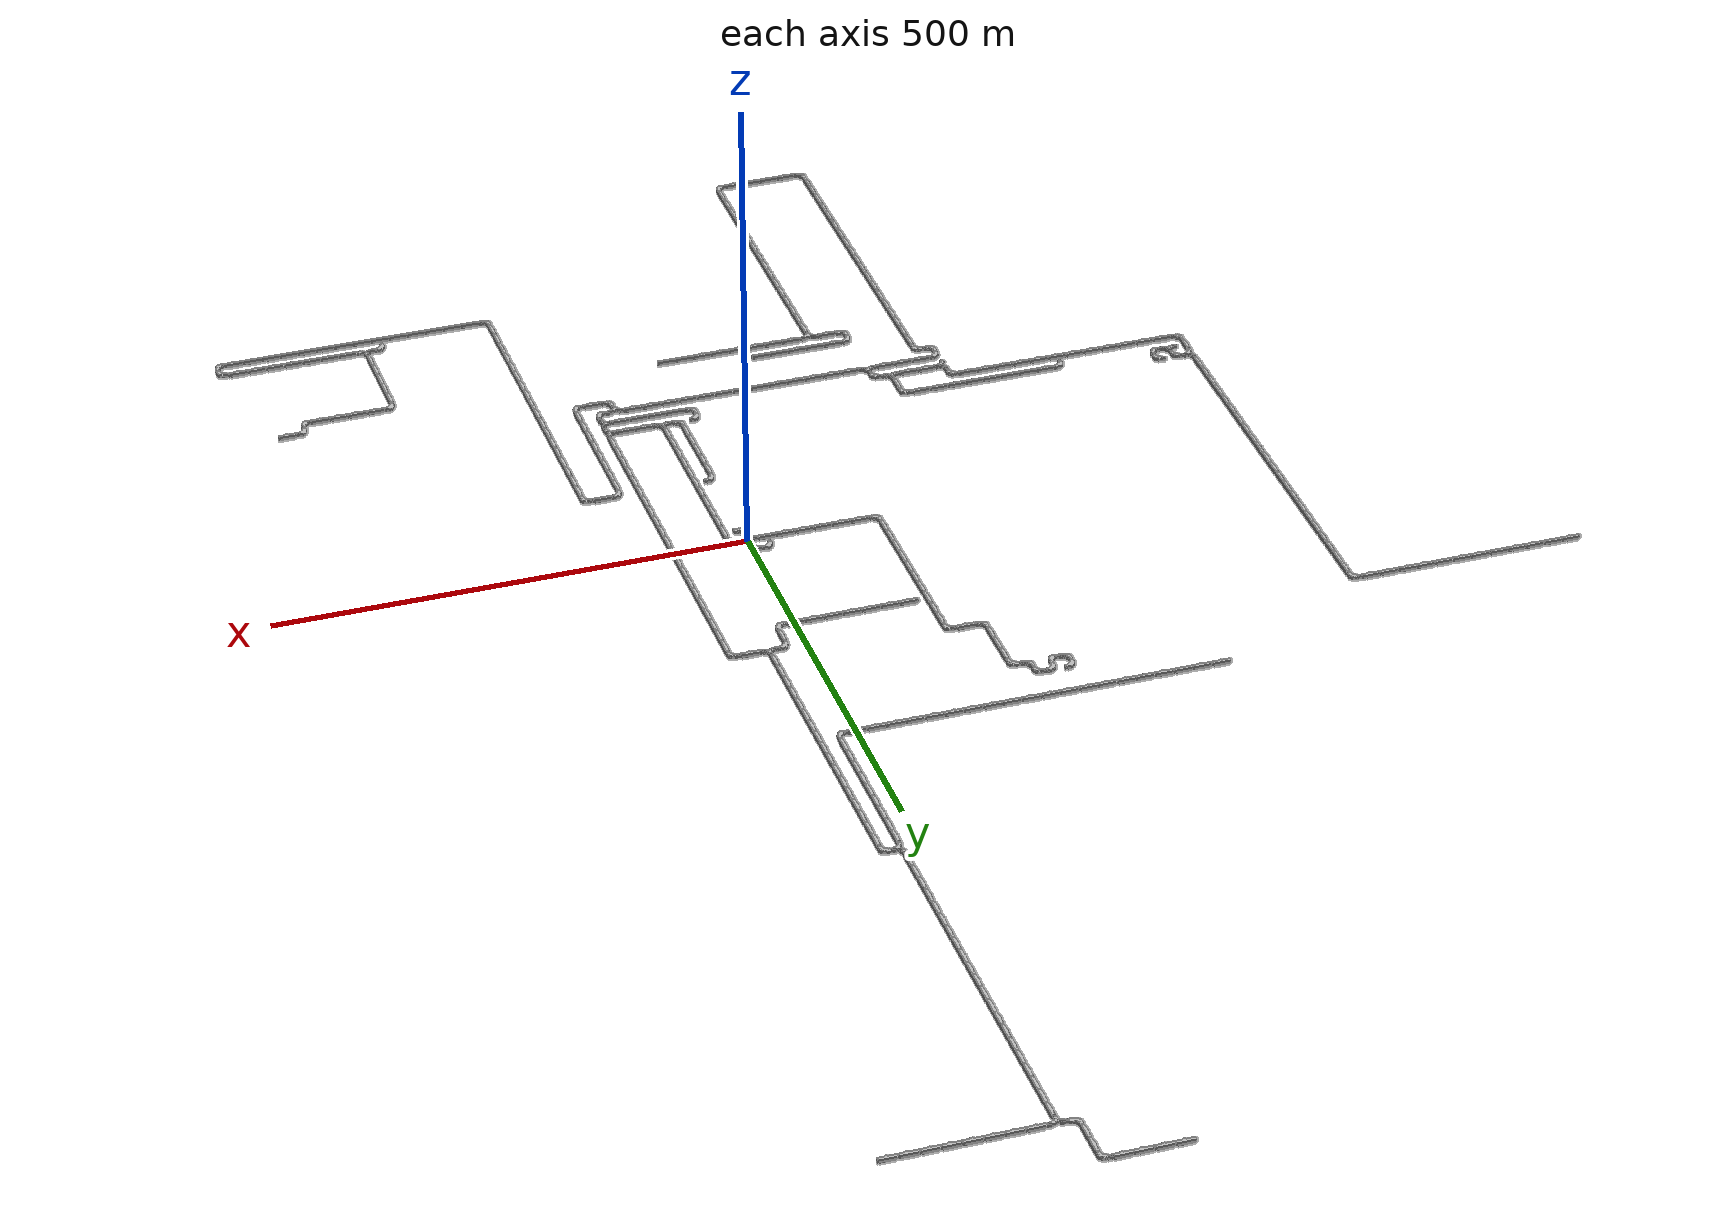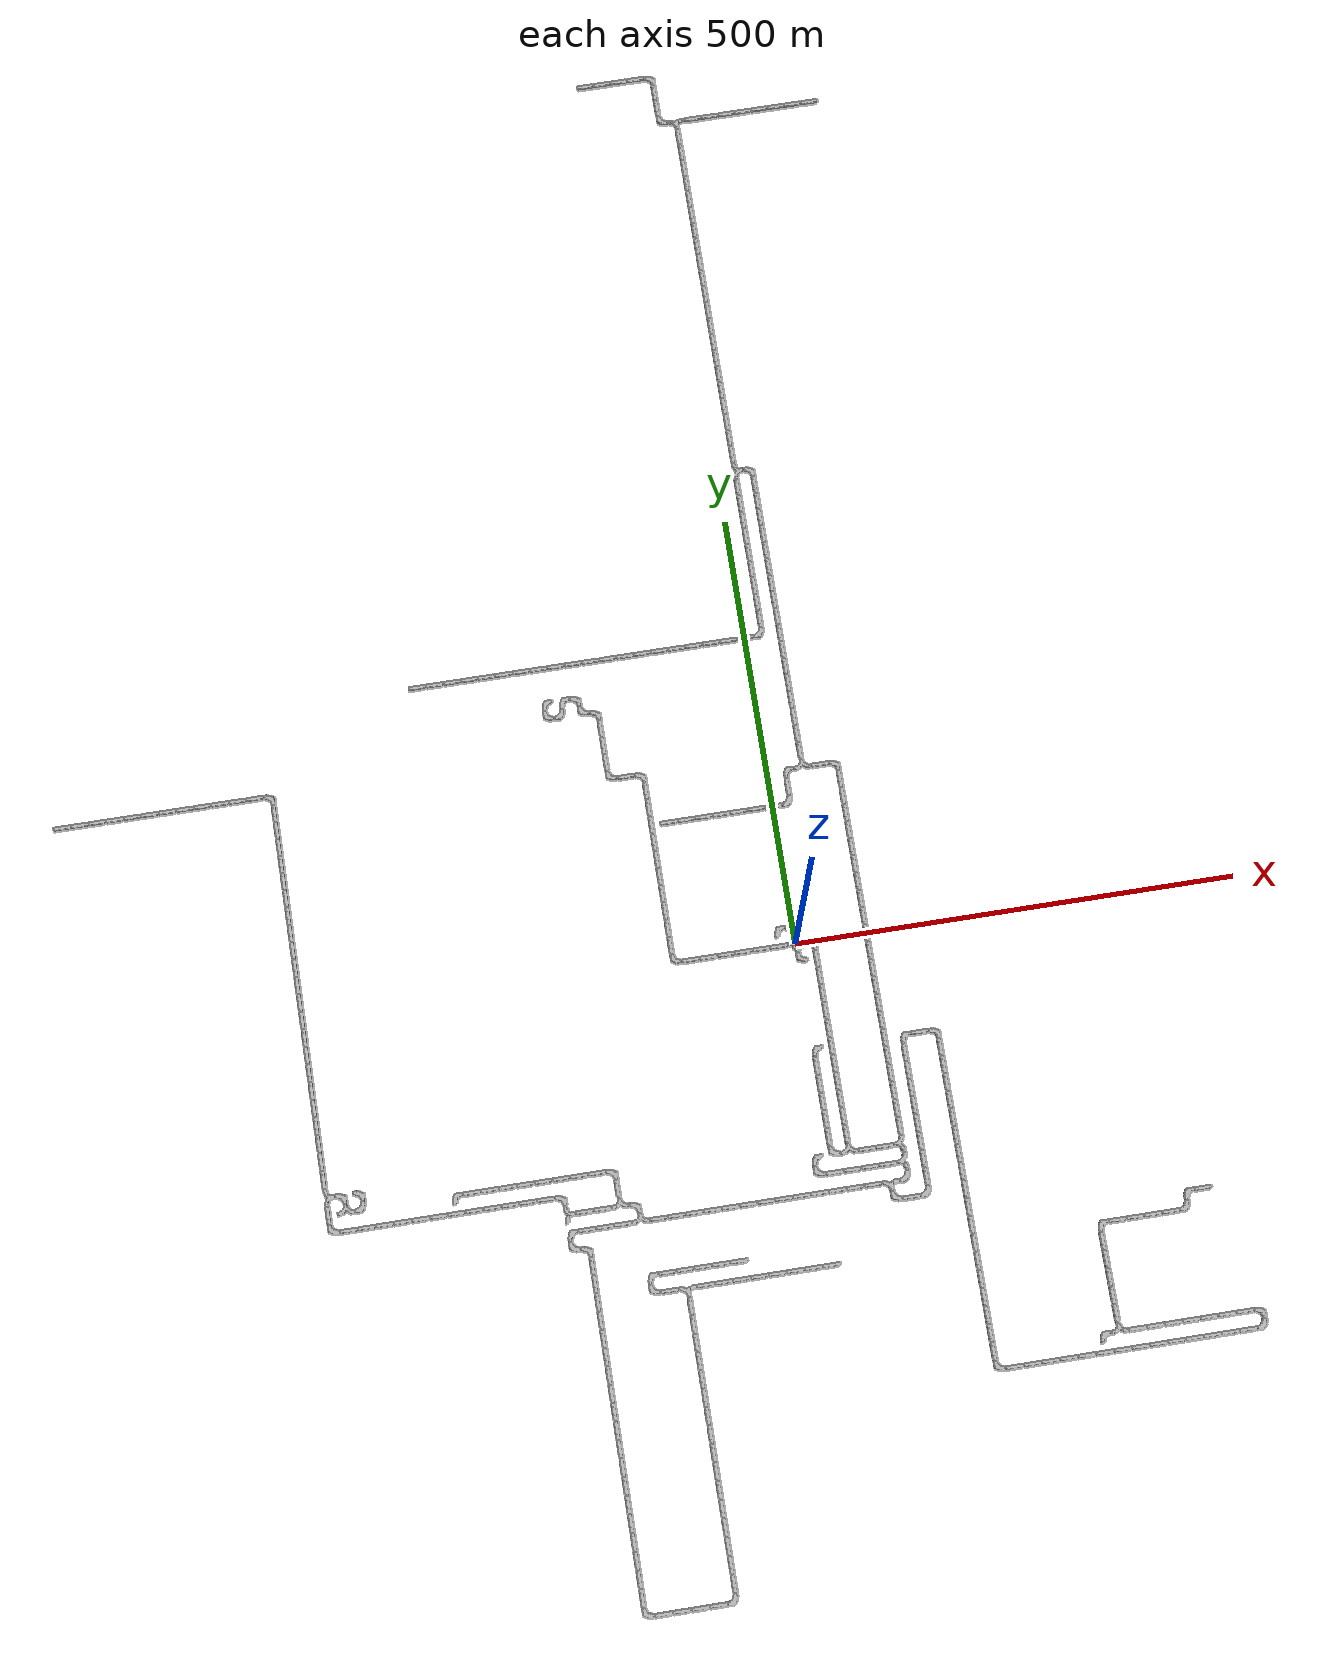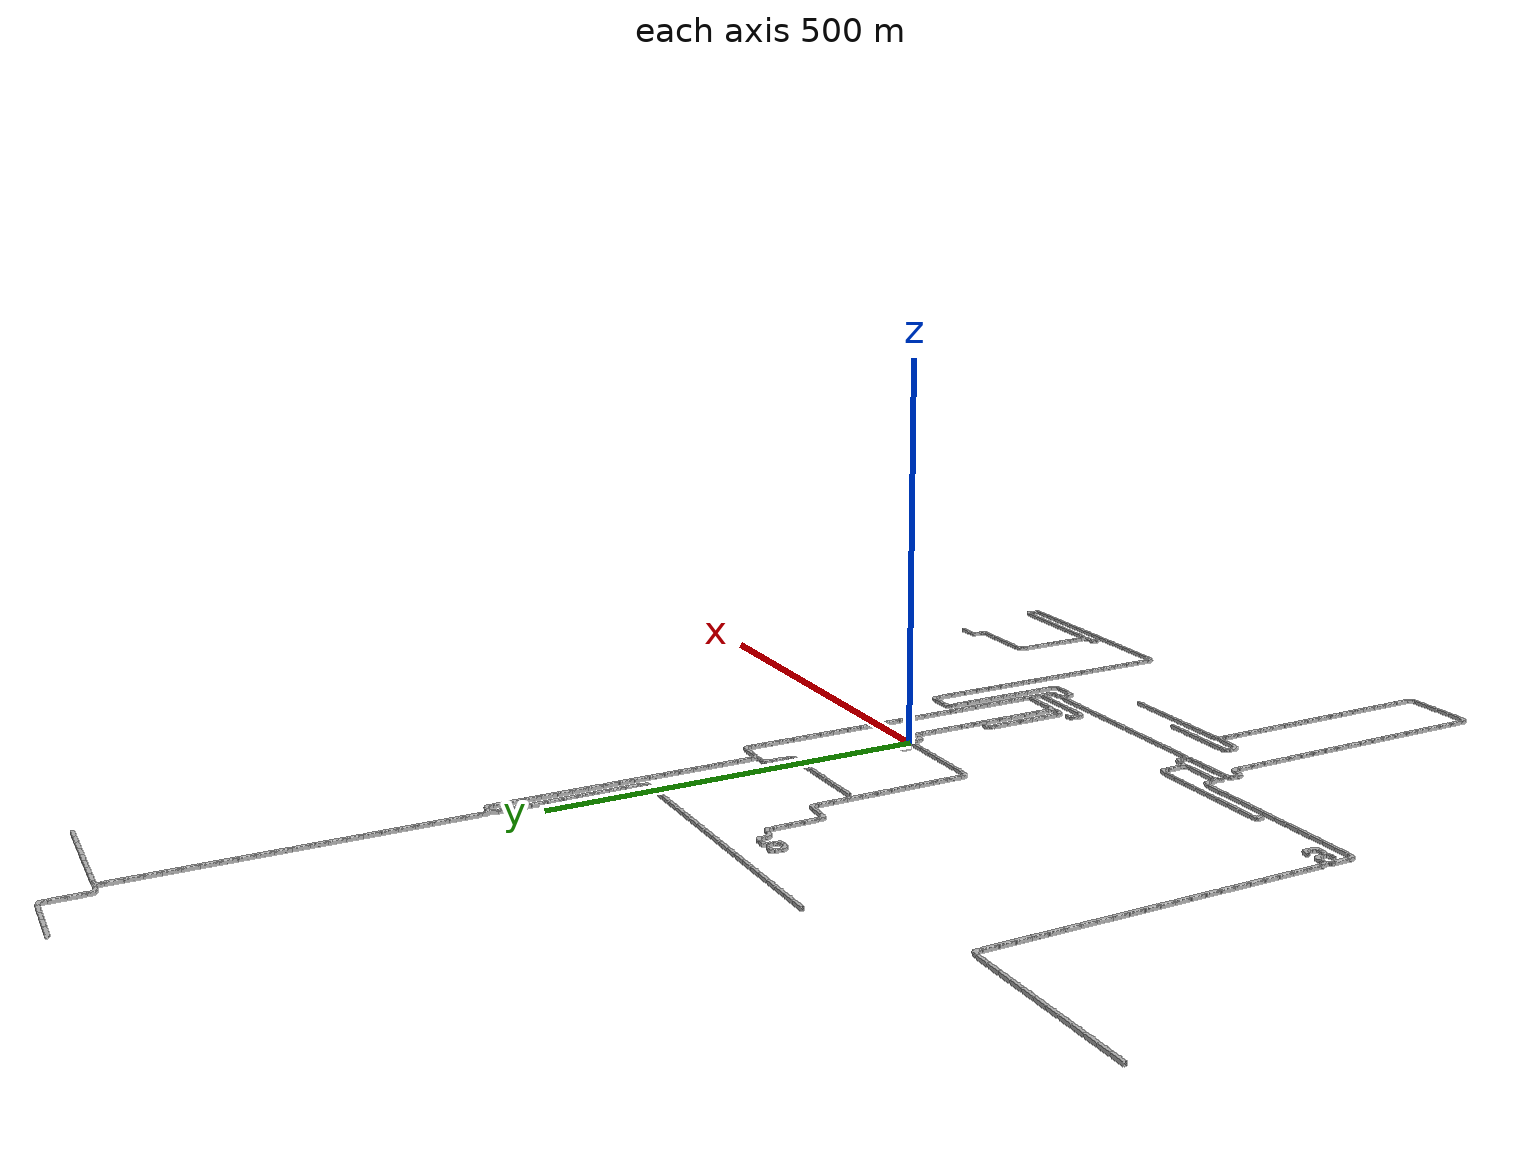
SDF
<sdf version="1.6">
 <world name="cave_8000_8">
  <include>
   <static>true</static>
   <name>cave_0_0</name>
   <pose>0 0 0 0 0 -1.5707963267948966</pose>
   <uri>model://cave_4way_20m</uri>
  </include>
  <include>
   <static>true</static>
   <name>cave_1_0</name>
   <pose>20 0 0 0 0 3.141592653589793</pose>
   <uri>model://cave_L_20m</uri>
  </include>
  <include>
   <static>true</static>
   <name>cave_1_-1</name>
   <pose>20 -20 0 0 0 0.0</pose>
   <uri>model://cave_straight_20m</uri>
  </include>
  <include>
   <static>true</static>
   <name>cave_1_-2</name>
   <pose>20 -40 0 0 0 0.0</pose>
   <uri>model://cave_straight_20m</uri>
  </include>
  <include>
   <static>true</static>
   <name>cave_1_-3</name>
   <pose>20 -60 0 0 0 0.0</pose>
   <uri>model://cave_straight_20m</uri>
  </include>
  <include>
   <static>true</static>
   <name>cave_1_-4</name>
   <pose>20 -80 0 0 0 0.0</pose>
   <uri>model://cave_straight_20m</uri>
  </include>
  <include>
   <static>true</static>
   <name>cave_1_-5</name>
   <pose>20 -100 0 0 0 0.0</pose>
   <uri>model://cave_straight_20m</uri>
  </include>
  <include>
   <static>true</static>
   <name>cave_1_-6</name>
   <pose>20 -120 0 0 0 0.0</pose>
   <uri>model://cave_straight_20m</uri>
  </include>
  <include>
   <static>true</static>
   <name>cave_1_-7</name>
   <pose>20 -140 0 0 0 0.0</pose>
   <uri>model://cave_straight_20m</uri>
  </include>
  <include>
   <static>true</static>
   <name>cave_1_-8</name>
   <pose>20 -160 0 0 0 0.0</pose>
   <uri>model://cave_straight_20m</uri>
  </include>
  <include>
   <static>true</static>
   <name>cave_1_-9</name>
   <pose>20 -180 0 0 0 0.0</pose>
   <uri>model://cave_straight_20m</uri>
  </include>
  <include>
   <static>true</static>
   <name>cave_1_-10</name>
   <pose>20 -200 0 0 0 0.0</pose>
   <uri>model://cave_straight_20m</uri>
  </include>
  <include>
   <static>true</static>
   <name>cave_1_-11</name>
   <pose>20 -220 0 0 0 0.0</pose>
   <uri>model://cave_straight_20m</uri>
  </include>
  <include>
   <static>true</static>
   <name>cave_1_-12</name>
   <pose>20 -240 0 0 0 0.0</pose>
   <uri>model://cave_3way_20m</uri>
  </include>
  <include>
   <static>true</static>
   <name>cave_2_-12</name>
   <pose>40 -240 0 0 0 1.5707963267948966</pose>
   <uri>model://cave_straight_20m</uri>
  </include>
  <include>
   <static>true</static>
   <name>cave_3_-12</name>
   <pose>60 -240 0 0 0 1.5707963267948966</pose>
   <uri>model://cave_straight_20m</uri>
  </include>
  <include>
   <static>true</static>
   <name>cave_4_-12</name>
   <pose>80 -240 0 0 0 1.5707963267948966</pose>
   <uri>model://cave_3way_20m</uri>
  </include>
  <include>
   <static>true</static>
   <name>cave_4_-13</name>
   <pose>80 -260 0 0 0 1.5707963267948966</pose>
   <uri>model://cave_3way_20m</uri>
  </include>
  <include>
   <static>true</static>
   <name>cave_4_-14</name>
   <pose>80 -280 0 0 0 1.5707963267948966</pose>
   <uri>model://cave_L_20m</uri>
  </include>
  <include>
   <static>true</static>
   <name>cave_3_-14</name>
   <pose>60 -280 0 0 0 3.141592653589793</pose>
   <uri>model://cave_3way_20m</uri>
  </include>
  <include>
   <static>true</static>
   <name>cave_3_-15</name>
   <pose>60 -300 0 0 0 0.0</pose>
   <uri>model://cave_L_20m</uri>
  </include>
  <include>
   <static>true</static>
   <name>cave_4_-15</name>
   <pose>80 -300 0 0 0 1.5707963267948966</pose>
   <uri>model://cave_straight_20m</uri>
  </include>
  <include>
   <static>true</static>
   <name>cave_5_-15</name>
   <pose>100 -300 0 0 0 1.5707963267948966</pose>
   <uri>model://cave_L_20m</uri>
  </include>
  <include>
   <static>true</static>
   <name>cave_5_-14</name>
   <pose>100 -280 0 0 0 0.0</pose>
   <uri>model://cave_straight_20m</uri>
  </include>
  <include>
   <static>true</static>
   <name>cave_5_-13</name>
   <pose>100 -260 0 0 0 0.0</pose>
   <uri>model://cave_straight_20m</uri>
  </include>
  <include>
   <static>true</static>
   <name>cave_5_-12</name>
   <pose>100 -240 0 0 0 0.0</pose>
   <uri>model://cave_straight_20m</uri>
  </include>
  <include>
   <static>true</static>
   <name>cave_5_-11</name>
   <pose>100 -220 0 0 0 0.0</pose>
   <uri>model://cave_straight_20m</uri>
  </include>
  <include>
   <static>true</static>
   <name>cave_5_-10</name>
   <pose>100 -200 0 0 0 0.0</pose>
   <uri>model://cave_straight_20m</uri>
  </include>
  <include>
   <static>true</static>
   <name>cave_5_-9</name>
   <pose>100 -180 0 0 0 0.0</pose>
   <uri>model://cave_straight_20m</uri>
  </include>
  <include>
   <static>true</static>
   <name>cave_5_-8</name>
   <pose>100 -160 0 0 0 0.0</pose>
   <uri>model://cave_straight_20m</uri>
  </include>
  <include>
   <static>true</static>
   <name>cave_5_-7</name>
   <pose>100 -140 0 0 0 0.0</pose>
   <uri>model://cave_straight_20m</uri>
  </include>
  <include>
   <static>true</static>
   <name>cave_5_-6</name>
   <pose>100 -120 0 0 0 -1.5707963267948966</pose>
   <uri>model://cave_L_20m</uri>
  </include>
  <include>
   <static>true</static>
   <name>cave_6_-6</name>
   <pose>120 -120 0 0 0 1.5707963267948966</pose>
   <uri>model://cave_straight_20m</uri>
  </include>
  <include>
   <static>true</static>
   <name>cave_7_-6</name>
   <pose>140 -120 0 0 0 3.141592653589793</pose>
   <uri>model://cave_L_20m</uri>
  </include>
  <include>
   <static>true</static>
   <name>cave_7_-7</name>
   <pose>140 -140 0 0 0 0.0</pose>
   <uri>model://cave_straight_20m</uri>
  </include>
  <include>
   <static>true</static>
   <name>cave_7_-8</name>
   <pose>140 -160 0 0 0 0.0</pose>
   <uri>model://cave_straight_20m</uri>
  </include>
  <include>
   <static>true</static>
   <name>cave_7_-9</name>
   <pose>140 -180 0 0 0 0.0</pose>
   <uri>model://cave_straight_20m</uri>
  </include>
  <include>
   <static>true</static>
   <name>cave_7_-10</name>
   <pose>140 -200 0 0 0 0.0</pose>
   <uri>model://cave_straight_20m</uri>
  </include>
  <include>
   <static>true</static>
   <name>cave_7_-11</name>
   <pose>140 -220 0 0 0 0.0</pose>
   <uri>model://cave_straight_20m</uri>
  </include>
  <include>
   <static>true</static>
   <name>cave_7_-12</name>
   <pose>140 -240 0 0 0 0.0</pose>
   <uri>model://cave_straight_20m</uri>
  </include>
  <include>
   <static>true</static>
   <name>cave_7_-13</name>
   <pose>140 -260 0 0 0 0.0</pose>
   <uri>model://cave_straight_20m</uri>
  </include>
  <include>
   <static>true</static>
   <name>cave_7_-14</name>
   <pose>140 -280 0 0 0 0.0</pose>
   <uri>model://cave_straight_20m</uri>
  </include>
  <include>
   <static>true</static>
   <name>cave_7_-15</name>
   <pose>140 -300 0 0 0 0.0</pose>
   <uri>model://cave_straight_20m</uri>
  </include>
  <include>
   <static>true</static>
   <name>cave_7_-16</name>
   <pose>140 -320 0 0 0 0.0</pose>
   <uri>model://cave_straight_20m</uri>
  </include>
  <include>
   <static>true</static>
   <name>cave_7_-17</name>
   <pose>140 -340 0 0 0 0.0</pose>
   <uri>model://cave_straight_20m</uri>
  </include>
  <include>
   <static>true</static>
   <name>cave_7_-18</name>
   <pose>140 -360 0 0 0 0.0</pose>
   <uri>model://cave_straight_20m</uri>
  </include>
  <include>
   <static>true</static>
   <name>cave_7_-19</name>
   <pose>140 -380 0 0 0 0.0</pose>
   <uri>model://cave_straight_20m</uri>
  </include>
  <include>
   <static>true</static>
   <name>cave_7_-20</name>
   <pose>140 -400 0 0 0 0.0</pose>
   <uri>model://cave_straight_20m</uri>
  </include>
  <include>
   <static>true</static>
   <name>cave_7_-21</name>
   <pose>140 -420 0 0 0 0.0</pose>
   <uri>model://cave_straight_20m</uri>
  </include>
  <include>
   <static>true</static>
   <name>cave_7_-22</name>
   <pose>140 -440 0 0 0 0.0</pose>
   <uri>model://cave_straight_20m</uri>
  </include>
  <include>
   <static>true</static>
   <name>cave_7_-23</name>
   <pose>140 -460 0 0 0 0.0</pose>
   <uri>model://cave_straight_20m</uri>
  </include>
  <include>
   <static>true</static>
   <name>cave_7_-24</name>
   <pose>140 -480 0 0 0 0.0</pose>
   <uri>model://cave_straight_20m</uri>
  </include>
  <include>
   <static>true</static>
   <name>cave_7_-25</name>
   <pose>140 -500 0 0 0 0.0</pose>
   <uri>model://cave_L_20m</uri>
  </include>
  <include>
   <static>true</static>
   <name>cave_8_-25</name>
   <pose>160 -500 0 0 0 1.5707963267948966</pose>
   <uri>model://cave_straight_20m</uri>
  </include>
  <include>
   <static>true</static>
   <name>cave_9_-25</name>
   <pose>180 -500 0 0 0 1.5707963267948966</pose>
   <uri>model://cave_straight_20m</uri>
  </include>
  <include>
   <static>true</static>
   <name>cave_10_-25</name>
   <pose>200 -500 0 0 0 1.5707963267948966</pose>
   <uri>model://cave_straight_20m</uri>
  </include>
  <include>
   <static>true</static>
   <name>cave_11_-25</name>
   <pose>220 -500 0 0 0 1.5707963267948966</pose>
   <uri>model://cave_straight_20m</uri>
  </include>
  <include>
   <static>true</static>
   <name>cave_12_-25</name>
   <pose>240 -500 0 0 0 1.5707963267948966</pose>
   <uri>model://cave_straight_20m</uri>
  </include>
  <include>
   <static>true</static>
   <name>cave_13_-25</name>
   <pose>260 -500 0 0 0 1.5707963267948966</pose>
   <uri>model://cave_straight_20m</uri>
  </include>
  <include>
   <static>true</static>
   <name>cave_14_-25</name>
   <pose>280 -500 0 0 0 1.5707963267948966</pose>
   <uri>model://cave_straight_20m</uri>
  </include>
  <include>
   <static>true</static>
   <name>cave_15_-25</name>
   <pose>300 -500 0 0 0 1.5707963267948966</pose>
   <uri>model://cave_straight_20m</uri>
  </include>
  <include>
   <static>true</static>
   <name>cave_16_-25</name>
   <pose>320 -500 0 0 0 1.5707963267948966</pose>
   <uri>model://cave_straight_20m</uri>
  </include>
  <include>
   <static>true</static>
   <name>cave_17_-25</name>
   <pose>340 -500 0 0 0 1.5707963267948966</pose>
   <uri>model://cave_straight_20m</uri>
  </include>
  <include>
   <static>true</static>
   <name>cave_18_-25</name>
   <pose>360 -500 0 0 0 1.5707963267948966</pose>
   <uri>model://cave_straight_20m</uri>
  </include>
  <include>
   <static>true</static>
   <name>cave_19_-25</name>
   <pose>380 -500 0 0 0 1.5707963267948966</pose>
   <uri>model://cave_straight_20m</uri>
  </include>
  <include>
   <static>true</static>
   <name>cave_20_-25</name>
   <pose>400 -500 0 0 0 1.5707963267948966</pose>
   <uri>model://cave_straight_20m</uri>
  </include>
  <include>
   <static>true</static>
   <name>cave_21_-25</name>
   <pose>420 -500 0 0 0 1.5707963267948966</pose>
   <uri>model://cave_straight_20m</uri>
  </include>
  <include>
   <static>true</static>
   <name>cave_22_-25</name>
   <pose>440 -500 0 0 0 1.5707963267948966</pose>
   <uri>model://cave_L_20m</uri>
  </include>
  <include>
   <static>true</static>
   <name>cave_22_-24</name>
   <pose>440 -480 0 0 0 3.141592653589793</pose>
   <uri>model://cave_L_20m</uri>
  </include>
  <include>
   <static>true</static>
   <name>cave_21_-24</name>
   <pose>420 -480 0 0 0 1.5707963267948966</pose>
   <uri>model://cave_straight_20m</uri>
  </include>
  <include>
   <static>true</static>
   <name>cave_20_-24</name>
   <pose>400 -480 0 0 0 1.5707963267948966</pose>
   <uri>model://cave_straight_20m</uri>
  </include>
  <include>
   <static>true</static>
   <name>cave_19_-24</name>
   <pose>380 -480 0 0 0 1.5707963267948966</pose>
   <uri>model://cave_straight_20m</uri>
  </include>
  <include>
   <static>true</static>
   <name>cave_18_-24</name>
   <pose>360 -480 0 0 0 1.5707963267948966</pose>
   <uri>model://cave_straight_20m</uri>
  </include>
  <include>
   <static>true</static>
   <name>cave_17_-24</name>
   <pose>340 -480 0 0 0 1.5707963267948966</pose>
   <uri>model://cave_straight_20m</uri>
  </include>
  <include>
   <static>true</static>
   <name>cave_16_-24</name>
   <pose>320 -480 0 0 0 1.5707963267948966</pose>
   <uri>model://cave_straight_20m</uri>
  </include>
  <include>
   <static>true</static>
   <name>cave_15_-24</name>
   <pose>300 -480 0 0 0 1.5707963267948966</pose>
   <uri>model://cave_straight_20m</uri>
  </include>
  <include>
   <static>true</static>
   <name>cave_14_-24</name>
   <pose>280 -480 0 0 0 0.0</pose>
   <uri>model://cave_3way_20m</uri>
  </include>
  <include>
   <static>true</static>
   <name>cave_13_-24</name>
   <pose>260 -480 0 0 0 -1.5707963267948966</pose>
   <uri>model://cave_L_20m</uri>
  </include>
  <include>
   <static>true</static>
   <name>cave_14_-23</name>
   <pose>280 -460 0 0 0 0.0</pose>
   <uri>model://cave_straight_20m</uri>
  </include>
  <include>
   <static>true</static>
   <name>cave_14_-22</name>
   <pose>280 -440 0 0 0 0.0</pose>
   <uri>model://cave_straight_20m</uri>
  </include>
  <include>
   <static>true</static>
   <name>cave_14_-21</name>
   <pose>280 -420 0 0 0 0.0</pose>
   <uri>model://cave_straight_20m</uri>
  </include>
  <include>
   <static>true</static>
   <name>cave_14_-20</name>
   <pose>280 -400 0 0 0 0.0</pose>
   <uri>model://cave_straight_20m</uri>
  </include>
  <include>
   <static>true</static>
   <name>cave_14_-19</name>
   <pose>280 -380 0 0 0 0.0</pose>
   <uri>model://cave_straight_20m</uri>
  </include>
  <include>
   <static>true</static>
   <name>cave_14_-18</name>
   <pose>280 -360 0 0 0 -1.5707963267948966</pose>
   <uri>model://cave_L_20m</uri>
  </include>
  <include>
   <static>true</static>
   <name>cave_15_-18</name>
   <pose>300 -360 0 0 0 1.5707963267948966</pose>
   <uri>model://cave_straight_20m</uri>
  </include>
  <include>
   <static>true</static>
   <name>cave_16_-18</name>
   <pose>320 -360 0 0 0 1.5707963267948966</pose>
   <uri>model://cave_straight_20m</uri>
  </include>
  <include>
   <static>true</static>
   <name>cave_17_-18</name>
   <pose>340 -360 0 0 0 1.5707963267948966</pose>
   <uri>model://cave_straight_20m</uri>
  </include>
  <include>
   <static>true</static>
   <name>cave_18_-18</name>
   <pose>360 -360 0 0 0 1.5707963267948966</pose>
   <uri>model://cave_straight_20m</uri>
  </include>
  <include>
   <static>true</static>
   <name>cave_19_-18</name>
   <pose>380 -360 0 0 0 1.5707963267948966</pose>
   <uri>model://cave_L_20m</uri>
  </include>
  <include>
   <static>true</static>
   <name>cave_19_-17</name>
   <pose>380 -340 0 0 0 -1.5707963267948966</pose>
   <uri>model://cave_L_20m</uri>
  </include>
  <include>
   <static>true</static>
   <name>cave_20_-17</name>
   <pose>400 -340 0 0 0 1.5707963267948966</pose>
   <uri>model://cave_straight_20m</uri>
  </include>
  <include>
   <static>true</static>
   <name>cave_2_-14</name>
   <pose>40 -280 0 0 0 1.5707963267948966</pose>
   <uri>model://cave_straight_20m</uri>
  </include>
  <include>
   <static>true</static>
   <name>cave_1_-14</name>
   <pose>20 -280 0 0 0 1.5707963267948966</pose>
   <uri>model://cave_straight_20m</uri>
  </include>
  <include>
   <static>true</static>
   <name>cave_0_-14</name>
   <pose>0 -280 0 0 0 1.5707963267948966</pose>
   <uri>model://cave_straight_20m</uri>
  </include>
  <include>
   <static>true</static>
   <name>cave_-1_-14</name>
   <pose>-20 -280 0 0 0 1.5707963267948966</pose>
   <uri>model://cave_straight_20m</uri>
  </include>
  <include>
   <static>true</static>
   <name>cave_-2_-14</name>
   <pose>-40 -280 0 0 0 1.5707963267948966</pose>
   <uri>model://cave_straight_20m</uri>
  </include>
  <include>
   <static>true</static>
   <name>cave_-3_-14</name>
   <pose>-60 -280 0 0 0 1.5707963267948966</pose>
   <uri>model://cave_straight_20m</uri>
  </include>
  <include>
   <static>true</static>
   <name>cave_-4_-14</name>
   <pose>-80 -280 0 0 0 1.5707963267948966</pose>
   <uri>model://cave_straight_20m</uri>
  </include>
  <include>
   <static>true</static>
   <name>cave_-5_-14</name>
   <pose>-100 -280 0 0 0 1.5707963267948966</pose>
   <uri>model://cave_straight_20m</uri>
  </include>
  <include>
   <static>true</static>
   <name>cave_-6_-14</name>
   <pose>-120 -280 0 0 0 1.5707963267948966</pose>
   <uri>model://cave_straight_20m</uri>
  </include>
  <include>
   <static>true</static>
   <name>cave_-7_-14</name>
   <pose>-140 -280 0 0 0 1.5707963267948966</pose>
   <uri>model://cave_straight_20m</uri>
  </include>
  <include>
   <static>true</static>
   <name>cave_-8_-14</name>
   <pose>-160 -280 0 0 0 1.5707963267948966</pose>
   <uri>model://cave_straight_20m</uri>
  </include>
  <include>
   <static>true</static>
   <name>cave_-9_-14</name>
   <pose>-180 -280 0 0 0 1.5707963267948966</pose>
   <uri>model://cave_straight_20m</uri>
  </include>
  <include>
   <static>true</static>
   <name>cave_-10_-14</name>
   <pose>-200 -280 0 0 0 1.5707963267948966</pose>
   <uri>model://cave_straight_20m</uri>
  </include>
  <include>
   <static>true</static>
   <name>cave_-11_-14</name>
   <pose>-220 -280 0 0 0 0.0</pose>
   <uri>model://cave_3way_20m</uri>
  </include>
  <include>
   <static>true</static>
   <name>cave_-12_-14</name>
   <pose>-240 -280 0 0 0 1.5707963267948966</pose>
   <uri>model://cave_straight_20m</uri>
  </include>
  <include>
   <static>true</static>
   <name>cave_-13_-14</name>
   <pose>-260 -280 0 0 0 1.5707963267948966</pose>
   <uri>model://cave_straight_20m</uri>
  </include>
  <include>
   <static>true</static>
   <name>cave_-14_-14</name>
   <pose>-280 -280 0 0 0 1.5707963267948966</pose>
   <uri>model://cave_straight_20m</uri>
  </include>
  <include>
   <static>true</static>
   <name>cave_-15_-14</name>
   <pose>-300 -280 0 0 0 -1.5707963267948966</pose>
   <uri>model://cave_L_20m</uri>
  </include>
  <include>
   <static>true</static>
   <name>cave_-15_-15</name>
   <pose>-300 -300 0 0 0 0.0</pose>
   <uri>model://cave_L_20m</uri>
  </include>
  <include>
   <static>true</static>
   <name>cave_-14_-15</name>
   <pose>-280 -300 0 0 0 3.141592653589793</pose>
   <uri>model://cave_L_20m</uri>
  </include>
  <include>
   <static>true</static>
   <name>cave_-14_-16</name>
   <pose>-280 -320 0 0 0 0.0</pose>
   <uri>model://cave_straight_20m</uri>
  </include>
  <include>
   <static>true</static>
   <name>cave_-14_-17</name>
   <pose>-280 -340 0 0 0 0.0</pose>
   <uri>model://cave_straight_20m</uri>
  </include>
  <include>
   <static>true</static>
   <name>cave_-14_-18</name>
   <pose>-280 -360 0 0 0 0.0</pose>
   <uri>model://cave_straight_20m</uri>
  </include>
  <include>
   <static>true</static>
   <name>cave_-14_-19</name>
   <pose>-280 -380 0 0 0 0.0</pose>
   <uri>model://cave_straight_20m</uri>
  </include>
  <include>
   <static>true</static>
   <name>cave_-14_-20</name>
   <pose>-280 -400 0 0 0 0.0</pose>
   <uri>model://cave_straight_20m</uri>
  </include>
  <include>
   <static>true</static>
   <name>cave_-14_-21</name>
   <pose>-280 -420 0 0 0 0.0</pose>
   <uri>model://cave_straight_20m</uri>
  </include>
  <include>
   <static>true</static>
   <name>cave_-14_-22</name>
   <pose>-280 -440 0 0 0 0.0</pose>
   <uri>model://cave_straight_20m</uri>
  </include>
  <include>
   <static>true</static>
   <name>cave_-14_-23</name>
   <pose>-280 -460 0 0 0 0.0</pose>
   <uri>model://cave_straight_20m</uri>
  </include>
  <include>
   <static>true</static>
   <name>cave_-14_-24</name>
   <pose>-280 -480 0 0 0 0.0</pose>
   <uri>model://cave_straight_20m</uri>
  </include>
  <include>
   <static>true</static>
   <name>cave_-14_-25</name>
   <pose>-280 -500 0 0 0 0.0</pose>
   <uri>model://cave_straight_20m</uri>
  </include>
  <include>
   <static>true</static>
   <name>cave_-14_-26</name>
   <pose>-280 -520 0 0 0 0.0</pose>
   <uri>model://cave_straight_20m</uri>
  </include>
  <include>
   <static>true</static>
   <name>cave_-14_-27</name>
   <pose>-280 -540 0 0 0 0.0</pose>
   <uri>model://cave_straight_20m</uri>
  </include>
  <include>
   <static>true</static>
   <name>cave_-14_-28</name>
   <pose>-280 -560 0 0 0 0.0</pose>
   <uri>model://cave_straight_20m</uri>
  </include>
  <include>
   <static>true</static>
   <name>cave_-14_-29</name>
   <pose>-280 -580 0 0 0 0.0</pose>
   <uri>model://cave_straight_20m</uri>
  </include>
  <include>
   <static>true</static>
   <name>cave_-14_-30</name>
   <pose>-280 -600 0 0 0 0.0</pose>
   <uri>model://cave_straight_20m</uri>
  </include>
  <include>
   <static>true</static>
   <name>cave_-14_-31</name>
   <pose>-280 -620 0 0 0 0.0</pose>
   <uri>model://cave_straight_20m</uri>
  </include>
  <include>
   <static>true</static>
   <name>cave_-14_-32</name>
   <pose>-280 -640 0 0 0 0.0</pose>
   <uri>model://cave_straight_20m</uri>
  </include>
  <include>
   <static>true</static>
   <name>cave_-14_-33</name>
   <pose>-280 -660 0 0 0 0.0</pose>
   <uri>model://cave_straight_20m</uri>
  </include>
  <include>
   <static>true</static>
   <name>cave_-14_-34</name>
   <pose>-280 -680 0 0 0 0.0</pose>
   <uri>model://cave_straight_20m</uri>
  </include>
  <include>
   <static>true</static>
   <name>cave_-14_-35</name>
   <pose>-280 -700 0 0 0 0.0</pose>
   <uri>model://cave_L_20m</uri>
  </include>
  <include>
   <static>true</static>
   <name>cave_-13_-35</name>
   <pose>-260 -700 0 0 0 1.5707963267948966</pose>
   <uri>model://cave_straight_20m</uri>
  </include>
  <include>
   <static>true</static>
   <name>cave_-12_-35</name>
   <pose>-240 -700 0 0 0 1.5707963267948966</pose>
   <uri>model://cave_straight_20m</uri>
  </include>
  <include>
   <static>true</static>
   <name>cave_-11_-35</name>
   <pose>-220 -700 0 0 0 1.5707963267948966</pose>
   <uri>model://cave_straight_20m</uri>
  </include>
  <include>
   <static>true</static>
   <name>cave_-10_-35</name>
   <pose>-200 -700 0 0 0 1.5707963267948966</pose>
   <uri>model://cave_straight_20m</uri>
  </include>
  <include>
   <static>true</static>
   <name>cave_-9_-35</name>
   <pose>-180 -700 0 0 0 1.5707963267948966</pose>
   <uri>model://cave_L_20m</uri>
  </include>
  <include>
   <static>true</static>
   <name>cave_-9_-34</name>
   <pose>-180 -680 0 0 0 0.0</pose>
   <uri>model://cave_straight_20m</uri>
  </include>
  <include>
   <static>true</static>
   <name>cave_-9_-33</name>
   <pose>-180 -660 0 0 0 0.0</pose>
   <uri>model://cave_straight_20m</uri>
  </include>
  <include>
   <static>true</static>
   <name>cave_-9_-32</name>
   <pose>-180 -640 0 0 0 0.0</pose>
   <uri>model://cave_straight_20m</uri>
  </include>
  <include>
   <static>true</static>
   <name>cave_-9_-31</name>
   <pose>-180 -620 0 0 0 0.0</pose>
   <uri>model://cave_straight_20m</uri>
  </include>
  <include>
   <static>true</static>
   <name>cave_-9_-30</name>
   <pose>-180 -600 0 0 0 0.0</pose>
   <uri>model://cave_straight_20m</uri>
  </include>
  <include>
   <static>true</static>
   <name>cave_-9_-29</name>
   <pose>-180 -580 0 0 0 0.0</pose>
   <uri>model://cave_straight_20m</uri>
  </include>
  <include>
   <static>true</static>
   <name>cave_-9_-28</name>
   <pose>-180 -560 0 0 0 0.0</pose>
   <uri>model://cave_straight_20m</uri>
  </include>
  <include>
   <static>true</static>
   <name>cave_-9_-27</name>
   <pose>-180 -540 0 0 0 0.0</pose>
   <uri>model://cave_straight_20m</uri>
  </include>
  <include>
   <static>true</static>
   <name>cave_-9_-26</name>
   <pose>-180 -520 0 0 0 0.0</pose>
   <uri>model://cave_straight_20m</uri>
  </include>
  <include>
   <static>true</static>
   <name>cave_-9_-25</name>
   <pose>-180 -500 0 0 0 0.0</pose>
   <uri>model://cave_straight_20m</uri>
  </include>
  <include>
   <static>true</static>
   <name>cave_-9_-24</name>
   <pose>-180 -480 0 0 0 0.0</pose>
   <uri>model://cave_straight_20m</uri>
  </include>
  <include>
   <static>true</static>
   <name>cave_-9_-23</name>
   <pose>-180 -460 0 0 0 0.0</pose>
   <uri>model://cave_straight_20m</uri>
  </include>
  <include>
   <static>true</static>
   <name>cave_-9_-22</name>
   <pose>-180 -440 0 0 0 0.0</pose>
   <uri>model://cave_straight_20m</uri>
  </include>
  <include>
   <static>true</static>
   <name>cave_-9_-21</name>
   <pose>-180 -420 0 0 0 0.0</pose>
   <uri>model://cave_straight_20m</uri>
  </include>
  <include>
   <static>true</static>
   <name>cave_-9_-20</name>
   <pose>-180 -400 0 0 0 0.0</pose>
   <uri>model://cave_straight_20m</uri>
  </include>
  <include>
   <static>true</static>
   <name>cave_-9_-19</name>
   <pose>-180 -380 0 0 0 0.0</pose>
   <uri>model://cave_straight_20m</uri>
  </include>
  <include>
   <static>true</static>
   <name>cave_-9_-18</name>
   <pose>-180 -360 0 0 0 3.141592653589793</pose>
   <uri>model://cave_3way_20m</uri>
  </include>
  <include>
   <static>true</static>
   <name>cave_-8_-18</name>
   <pose>-160 -360 0 0 0 1.5707963267948966</pose>
   <uri>model://cave_straight_20m</uri>
  </include>
  <include>
   <static>true</static>
   <name>cave_-7_-18</name>
   <pose>-140 -360 0 0 0 1.5707963267948966</pose>
   <uri>model://cave_straight_20m</uri>
  </include>
  <include>
   <static>true</static>
   <name>cave_-6_-18</name>
   <pose>-120 -360 0 0 0 1.5707963267948966</pose>
   <uri>model://cave_straight_20m</uri>
  </include>
  <include>
   <static>true</static>
   <name>cave_-5_-18</name>
   <pose>-100 -360 0 0 0 1.5707963267948966</pose>
   <uri>model://cave_straight_20m</uri>
  </include>
  <include>
   <static>true</static>
   <name>cave_-4_-18</name>
   <pose>-80 -360 0 0 0 1.5707963267948966</pose>
   <uri>model://cave_straight_20m</uri>
  </include>
  <include>
   <static>true</static>
   <name>cave_-3_-18</name>
   <pose>-60 -360 0 0 0 1.5707963267948966</pose>
   <uri>model://cave_straight_20m</uri>
  </include>
  <include>
   <static>true</static>
   <name>cave_-2_-18</name>
   <pose>-40 -360 0 0 0 1.5707963267948966</pose>
   <uri>model://cave_straight_20m</uri>
  </include>
  <include>
   <static>true</static>
   <name>cave_-1_-18</name>
   <pose>-20 -360 0 0 0 1.5707963267948966</pose>
   <uri>model://cave_straight_20m</uri>
  </include>
  <include>
   <static>true</static>
   <name>cave_-10_-18</name>
   <pose>-200 -360 0 0 0 1.5707963267948966</pose>
   <uri>model://cave_straight_20m</uri>
  </include>
  <include>
   <static>true</static>
   <name>cave_-11_-18</name>
   <pose>-220 -360 0 0 0 0.0</pose>
   <uri>model://cave_L_20m</uri>
  </include>
  <include>
   <static>true</static>
   <name>cave_-11_-17</name>
   <pose>-220 -340 0 0 0 -1.5707963267948966</pose>
   <uri>model://cave_L_20m</uri>
  </include>
  <include>
   <static>true</static>
   <name>cave_-10_-17</name>
   <pose>-200 -340 0 0 0 1.5707963267948966</pose>
   <uri>model://cave_straight_20m</uri>
  </include>
  <include>
   <static>true</static>
   <name>cave_-9_-17</name>
   <pose>-180 -340 0 0 0 1.5707963267948966</pose>
   <uri>model://cave_straight_20m</uri>
  </include>
  <include>
   <static>true</static>
   <name>cave_-8_-17</name>
   <pose>-160 -340 0 0 0 1.5707963267948966</pose>
   <uri>model://cave_straight_20m</uri>
  </include>
  <include>
   <static>true</static>
   <name>cave_-7_-17</name>
   <pose>-140 -340 0 0 0 1.5707963267948966</pose>
   <uri>model://cave_straight_20m</uri>
  </include>
  <include>
   <static>true</static>
   <name>cave_-6_-17</name>
   <pose>-120 -340 0 0 0 1.5707963267948966</pose>
   <uri>model://cave_straight_20m</uri>
  </include>
  <include>
   <static>true</static>
   <name>cave_-11_-13</name>
   <pose>-220 -260 0 0 0 3.141592653589793</pose>
   <uri>model://cave_L_20m</uri>
  </include>
  <include>
   <static>true</static>
   <name>cave_-12_-13</name>
   <pose>-240 -260 0 0 0 0.0</pose>
   <uri>model://cave_3way_20m</uri>
  </include>
  <include>
   <static>true</static>
   <name>cave_-13_-13</name>
   <pose>-260 -260 0 0 0 1.5707963267948966</pose>
   <uri>model://cave_straight_20m</uri>
  </include>
  <include>
   <static>true</static>
   <name>cave_-14_-13</name>
   <pose>-280 -260 0 0 0 1.5707963267948966</pose>
   <uri>model://cave_straight_20m</uri>
  </include>
  <include>
   <static>true</static>
   <name>cave_-15_-13</name>
   <pose>-300 -260 0 0 0 -1.5707963267948966</pose>
   <uri>model://cave_3way_20m</uri>
  </include>
  <include>
   <static>true</static>
   <name>cave_-15_-12</name>
   <pose>-300 -240 0 0 0 3.141592653589793</pose>
   <uri>model://cave_L_20m</uri>
  </include>
  <include>
   <static>true</static>
   <name>cave_-16_-12</name>
   <pose>-320 -240 0 0 0 1.5707963267948966</pose>
   <uri>model://cave_straight_20m</uri>
  </include>
  <include>
   <static>true</static>
   <name>cave_-17_-12</name>
   <pose>-340 -240 0 0 0 1.5707963267948966</pose>
   <uri>model://cave_straight_20m</uri>
  </include>
  <include>
   <static>true</static>
   <name>cave_-18_-12</name>
   <pose>-360 -240 0 0 0 1.5707963267948966</pose>
   <uri>model://cave_straight_20m</uri>
  </include>
  <include>
   <static>true</static>
   <name>cave_-19_-12</name>
   <pose>-380 -240 0 0 0 1.5707963267948966</pose>
   <uri>model://cave_straight_20m</uri>
  </include>
  <include>
   <static>true</static>
   <name>cave_-20_-12</name>
   <pose>-400 -240 0 0 0 1.5707963267948966</pose>
   <uri>model://cave_straight_20m</uri>
  </include>
  <include>
   <static>true</static>
   <name>cave_-21_-12</name>
   <pose>-420 -240 0 0 0 1.5707963267948966</pose>
   <uri>model://cave_straight_20m</uri>
  </include>
  <include>
   <static>true</static>
   <name>cave_-22_-12</name>
   <pose>-440 -240 0 0 0 1.5707963267948966</pose>
   <uri>model://cave_straight_20m</uri>
  </include>
  <include>
   <static>true</static>
   <name>cave_-23_-12</name>
   <pose>-460 -240 0 0 0 1.5707963267948966</pose>
   <uri>model://cave_straight_20m</uri>
  </include>
  <include>
   <static>true</static>
   <name>cave_-24_-12</name>
   <pose>-480 -240 0 0 0 1.5707963267948966</pose>
   <uri>model://cave_straight_20m</uri>
  </include>
  <include>
   <static>true</static>
   <name>cave_-25_-12</name>
   <pose>-500 -240 0 0 0 1.5707963267948966</pose>
   <uri>model://cave_straight_20m</uri>
  </include>
  <include>
   <static>true</static>
   <name>cave_-26_-12</name>
   <pose>-520 -240 0 0 0 1.5707963267948966</pose>
   <uri>model://cave_straight_20m</uri>
  </include>
  <include>
   <static>true</static>
   <name>cave_-27_-12</name>
   <pose>-540 -240 0 0 0 1.5707963267948966</pose>
   <uri>model://cave_straight_20m</uri>
  </include>
  <include>
   <static>true</static>
   <name>cave_-28_-12</name>
   <pose>-560 -240 0 0 0 0.0</pose>
   <uri>model://cave_L_20m</uri>
  </include>
  <include>
   <static>true</static>
   <name>cave_-28_-11</name>
   <pose>-560 -220 0 0 0 0.0</pose>
   <uri>model://cave_straight_20m</uri>
  </include>
  <include>
   <static>true</static>
   <name>cave_-28_-10</name>
   <pose>-560 -200 0 0 0 -1.5707963267948966</pose>
   <uri>model://cave_3way_20m</uri>
  </include>
  <include>
   <static>true</static>
   <name>cave_-27_-10</name>
   <pose>-540 -200 0 0 0 3.141592653589793</pose>
   <uri>model://cave_L_20m</uri>
  </include>
  <include>
   <static>true</static>
   <name>cave_-27_-11</name>
   <pose>-540 -220 0 0 0 0.0</pose>
   <uri>model://cave_3way_20m</uri>
  </include>
  <include>
   <static>true</static>
   <name>cave_-26_-11</name>
   <pose>-520 -220 0 0 0 1.5707963267948966</pose>
   <uri>model://cave_L_20m</uri>
  </include>
  <include>
   <static>true</static>
   <name>cave_-26_-10</name>
   <pose>-520 -200 0 0 0 3.141592653589793</pose>
   <uri>model://cave_L_20m</uri>
  </include>
  <include>
   <static>true</static>
   <name>cave_-28_-9</name>
   <pose>-560 -180 0 0 0 0.0</pose>
   <uri>model://cave_straight_20m</uri>
  </include>
  <include>
   <static>true</static>
   <name>cave_-28_-8</name>
   <pose>-560 -160 0 0 0 0.0</pose>
   <uri>model://cave_straight_20m</uri>
  </include>
  <include>
   <static>true</static>
   <name>cave_-28_-7</name>
   <pose>-560 -140 0 0 0 0.0</pose>
   <uri>model://cave_straight_20m</uri>
  </include>
  <include>
   <static>true</static>
   <name>cave_-28_-6</name>
   <pose>-560 -120 0 0 0 0.0</pose>
   <uri>model://cave_straight_20m</uri>
  </include>
  <include>
   <static>true</static>
   <name>cave_-28_-5</name>
   <pose>-560 -100 0 0 0 0.0</pose>
   <uri>model://cave_straight_20m</uri>
  </include>
  <include>
   <static>true</static>
   <name>cave_-28_-4</name>
   <pose>-560 -80 0 0 0 0.0</pose>
   <uri>model://cave_straight_20m</uri>
  </include>
  <include>
   <static>true</static>
   <name>cave_-28_-3</name>
   <pose>-560 -60 0 0 0 0.0</pose>
   <uri>model://cave_straight_20m</uri>
  </include>
  <include>
   <static>true</static>
   <name>cave_-28_-2</name>
   <pose>-560 -40 0 0 0 0.0</pose>
   <uri>model://cave_straight_20m</uri>
  </include>
  <include>
   <static>true</static>
   <name>cave_-28_-1</name>
   <pose>-560 -20 0 0 0 0.0</pose>
   <uri>model://cave_straight_20m</uri>
  </include>
  <include>
   <static>true</static>
   <name>cave_-28_0</name>
   <pose>-560 0 0 0 0 0.0</pose>
   <uri>model://cave_straight_20m</uri>
  </include>
  <include>
   <static>true</static>
   <name>cave_-28_1</name>
   <pose>-560 20 0 0 0 0.0</pose>
   <uri>model://cave_straight_20m</uri>
  </include>
  <include>
   <static>true</static>
   <name>cave_-28_2</name>
   <pose>-560 40 0 0 0 0.0</pose>
   <uri>model://cave_straight_20m</uri>
  </include>
  <include>
   <static>true</static>
   <name>cave_-28_3</name>
   <pose>-560 60 0 0 0 0.0</pose>
   <uri>model://cave_straight_20m</uri>
  </include>
  <include>
   <static>true</static>
   <name>cave_-28_4</name>
   <pose>-560 80 0 0 0 0.0</pose>
   <uri>model://cave_straight_20m</uri>
  </include>
  <include>
   <static>true</static>
   <name>cave_-28_5</name>
   <pose>-560 100 0 0 0 0.0</pose>
   <uri>model://cave_straight_20m</uri>
  </include>
  <include>
   <static>true</static>
   <name>cave_-28_6</name>
   <pose>-560 120 0 0 0 0.0</pose>
   <uri>model://cave_straight_20m</uri>
  </include>
  <include>
   <static>true</static>
   <name>cave_-28_7</name>
   <pose>-560 140 0 0 0 0.0</pose>
   <uri>model://cave_straight_20m</uri>
  </include>
  <include>
   <static>true</static>
   <name>cave_-28_8</name>
   <pose>-560 160 0 0 0 0.0</pose>
   <uri>model://cave_straight_20m</uri>
  </include>
  <include>
   <static>true</static>
   <name>cave_-28_9</name>
   <pose>-560 180 0 0 0 0.0</pose>
   <uri>model://cave_straight_20m</uri>
  </include>
  <include>
   <static>true</static>
   <name>cave_-28_10</name>
   <pose>-560 200 0 0 0 0.0</pose>
   <uri>model://cave_straight_20m</uri>
  </include>
  <include>
   <static>true</static>
   <name>cave_-28_11</name>
   <pose>-560 220 0 0 0 0.0</pose>
   <uri>model://cave_straight_20m</uri>
  </include>
  <include>
   <static>true</static>
   <name>cave_-28_12</name>
   <pose>-560 240 0 0 0 0.0</pose>
   <uri>model://cave_straight_20m</uri>
  </include>
  <include>
   <static>true</static>
   <name>cave_-28_13</name>
   <pose>-560 260 0 0 0 3.141592653589793</pose>
   <uri>model://cave_L_20m</uri>
  </include>
  <include>
   <static>true</static>
   <name>cave_-29_13</name>
   <pose>-580 260 0 0 0 1.5707963267948966</pose>
   <uri>model://cave_straight_20m</uri>
  </include>
  <include>
   <static>true</static>
   <name>cave_-30_13</name>
   <pose>-600 260 0 0 0 1.5707963267948966</pose>
   <uri>model://cave_straight_20m</uri>
  </include>
  <include>
   <static>true</static>
   <name>cave_-31_13</name>
   <pose>-620 260 0 0 0 1.5707963267948966</pose>
   <uri>model://cave_straight_20m</uri>
  </include>
  <include>
   <static>true</static>
   <name>cave_-32_13</name>
   <pose>-640 260 0 0 0 1.5707963267948966</pose>
   <uri>model://cave_straight_20m</uri>
  </include>
  <include>
   <static>true</static>
   <name>cave_-33_13</name>
   <pose>-660 260 0 0 0 1.5707963267948966</pose>
   <uri>model://cave_straight_20m</uri>
  </include>
  <include>
   <static>true</static>
   <name>cave_-34_13</name>
   <pose>-680 260 0 0 0 1.5707963267948966</pose>
   <uri>model://cave_straight_20m</uri>
  </include>
  <include>
   <static>true</static>
   <name>cave_-35_13</name>
   <pose>-700 260 0 0 0 1.5707963267948966</pose>
   <uri>model://cave_straight_20m</uri>
  </include>
  <include>
   <static>true</static>
   <name>cave_-36_13</name>
   <pose>-720 260 0 0 0 1.5707963267948966</pose>
   <uri>model://cave_straight_20m</uri>
  </include>
  <include>
   <static>true</static>
   <name>cave_-37_13</name>
   <pose>-740 260 0 0 0 1.5707963267948966</pose>
   <uri>model://cave_straight_20m</uri>
  </include>
  <include>
   <static>true</static>
   <name>cave_-38_13</name>
   <pose>-760 260 0 0 0 1.5707963267948966</pose>
   <uri>model://cave_straight_20m</uri>
  </include>
  <include>
   <static>true</static>
   <name>cave_-39_13</name>
   <pose>-780 260 0 0 0 1.5707963267948966</pose>
   <uri>model://cave_straight_20m</uri>
  </include>
  <include>
   <static>true</static>
   <name>cave_-40_13</name>
   <pose>-800 260 0 0 0 1.5707963267948966</pose>
   <uri>model://cave_straight_20m</uri>
  </include>
  <include>
   <static>true</static>
   <name>cave_-12_-12</name>
   <pose>-240 -240 0 0 0 0.0</pose>
   <uri>model://cave_straight_20m</uri>
  </include>
  <include>
   <static>true</static>
   <name>cave_-12_-11</name>
   <pose>-240 -220 0 0 0 3.141592653589793</pose>
   <uri>model://cave_L_20m</uri>
  </include>
  <include>
   <static>true</static>
   <name>cave_-13_-11</name>
   <pose>-260 -220 0 0 0 1.5707963267948966</pose>
   <uri>model://cave_straight_20m</uri>
  </include>
  <include>
   <static>true</static>
   <name>cave_-14_-11</name>
   <pose>-280 -220 0 0 0 1.5707963267948966</pose>
   <uri>model://cave_straight_20m</uri>
  </include>
  <include>
   <static>true</static>
   <name>cave_-15_-11</name>
   <pose>-300 -220 0 0 0 1.5707963267948966</pose>
   <uri>model://cave_straight_20m</uri>
  </include>
  <include>
   <static>true</static>
   <name>cave_-16_-11</name>
   <pose>-320 -220 0 0 0 1.5707963267948966</pose>
   <uri>model://cave_straight_20m</uri>
  </include>
  <include>
   <static>true</static>
   <name>cave_-17_-11</name>
   <pose>-340 -220 0 0 0 1.5707963267948966</pose>
   <uri>model://cave_straight_20m</uri>
  </include>
  <include>
   <static>true</static>
   <name>cave_-18_-11</name>
   <pose>-360 -220 0 0 0 1.5707963267948966</pose>
   <uri>model://cave_straight_20m</uri>
  </include>
  <include>
   <static>true</static>
   <name>cave_-19_-11</name>
   <pose>-380 -220 0 0 0 1.5707963267948966</pose>
   <uri>model://cave_straight_20m</uri>
  </include>
  <include>
   <static>true</static>
   <name>cave_-20_-11</name>
   <pose>-400 -220 0 0 0 1.5707963267948966</pose>
   <uri>model://cave_straight_20m</uri>
  </include>
  <include>
   <static>true</static>
   <name>cave_-21_-11</name>
   <pose>-420 -220 0 0 0 -1.5707963267948966</pose>
   <uri>model://cave_L_20m</uri>
  </include>
  <include>
   <static>true</static>
   <name>cave_3_-13</name>
   <pose>60 -260 0 0 0 1.5707963267948966</pose>
   <uri>model://cave_straight_20m</uri>
  </include>
  <include>
   <static>true</static>
   <name>cave_2_-13</name>
   <pose>40 -260 0 0 0 1.5707963267948966</pose>
   <uri>model://cave_straight_20m</uri>
  </include>
  <include>
   <static>true</static>
   <name>cave_1_-13</name>
   <pose>20 -260 0 0 0 1.5707963267948966</pose>
   <uri>model://cave_straight_20m</uri>
  </include>
  <include>
   <static>true</static>
   <name>cave_0_-13</name>
   <pose>0 -260 0 0 0 1.5707963267948966</pose>
   <uri>model://cave_straight_20m</uri>
  </include>
  <include>
   <static>true</static>
   <name>cave_-1_-13</name>
   <pose>-20 -260 0 0 0 0.0</pose>
   <uri>model://cave_L_20m</uri>
  </include>
  <include>
   <static>true</static>
   <name>cave_-1_-12</name>
   <pose>-20 -240 0 0 0 -1.5707963267948966</pose>
   <uri>model://cave_L_20m</uri>
  </include>
  <include>
   <static>true</static>
   <name>cave_4_-11</name>
   <pose>80 -220 0 0 0 0.0</pose>
   <uri>model://cave_straight_20m</uri>
  </include>
  <include>
   <static>true</static>
   <name>cave_4_-10</name>
   <pose>80 -200 0 0 0 0.0</pose>
   <uri>model://cave_straight_20m</uri>
  </include>
  <include>
   <static>true</static>
   <name>cave_4_-9</name>
   <pose>80 -180 0 0 0 0.0</pose>
   <uri>model://cave_straight_20m</uri>
  </include>
  <include>
   <static>true</static>
   <name>cave_4_-8</name>
   <pose>80 -160 0 0 0 0.0</pose>
   <uri>model://cave_straight_20m</uri>
  </include>
  <include>
   <static>true</static>
   <name>cave_4_-7</name>
   <pose>80 -140 0 0 0 0.0</pose>
   <uri>model://cave_straight_20m</uri>
  </include>
  <include>
   <static>true</static>
   <name>cave_4_-6</name>
   <pose>80 -120 0 0 0 0.0</pose>
   <uri>model://cave_straight_20m</uri>
  </include>
  <include>
   <static>true</static>
   <name>cave_4_-5</name>
   <pose>80 -100 0 0 0 0.0</pose>
   <uri>model://cave_straight_20m</uri>
  </include>
  <include>
   <static>true</static>
   <name>cave_4_-4</name>
   <pose>80 -80 0 0 0 0.0</pose>
   <uri>model://cave_straight_20m</uri>
  </include>
  <include>
   <static>true</static>
   <name>cave_4_-3</name>
   <pose>80 -60 0 0 0 0.0</pose>
   <uri>model://cave_straight_20m</uri>
  </include>
  <include>
   <static>true</static>
   <name>cave_4_-2</name>
   <pose>80 -40 0 0 0 0.0</pose>
   <uri>model://cave_straight_20m</uri>
  </include>
  <include>
   <static>true</static>
   <name>cave_4_-1</name>
   <pose>80 -20 0 0 0 0.0</pose>
   <uri>model://cave_straight_20m</uri>
  </include>
  <include>
   <static>true</static>
   <name>cave_4_0</name>
   <pose>80 0 0 0 0 0.0</pose>
   <uri>model://cave_straight_20m</uri>
  </include>
  <include>
   <static>true</static>
   <name>cave_4_1</name>
   <pose>80 20 0 0 0 0.0</pose>
   <uri>model://cave_straight_20m</uri>
  </include>
  <include>
   <static>true</static>
   <name>cave_4_2</name>
   <pose>80 40 0 0 0 0.0</pose>
   <uri>model://cave_straight_20m</uri>
  </include>
  <include>
   <static>true</static>
   <name>cave_4_3</name>
   <pose>80 60 0 0 0 0.0</pose>
   <uri>model://cave_straight_20m</uri>
  </include>
  <include>
   <static>true</static>
   <name>cave_4_4</name>
   <pose>80 80 0 0 0 0.0</pose>
   <uri>model://cave_straight_20m</uri>
  </include>
  <include>
   <static>true</static>
   <name>cave_4_5</name>
   <pose>80 100 0 0 0 0.0</pose>
   <uri>model://cave_straight_20m</uri>
  </include>
  <include>
   <static>true</static>
   <name>cave_4_6</name>
   <pose>80 120 0 0 0 0.0</pose>
   <uri>model://cave_straight_20m</uri>
  </include>
  <include>
   <static>true</static>
   <name>cave_4_7</name>
   <pose>80 140 0 0 0 0.0</pose>
   <uri>model://cave_straight_20m</uri>
  </include>
  <include>
   <static>true</static>
   <name>cave_4_8</name>
   <pose>80 160 0 0 0 0.0</pose>
   <uri>model://cave_straight_20m</uri>
  </include>
  <include>
   <static>true</static>
   <name>cave_4_9</name>
   <pose>80 180 0 0 0 0.0</pose>
   <uri>model://cave_straight_20m</uri>
  </include>
  <include>
   <static>true</static>
   <name>cave_4_10</name>
   <pose>80 200 0 0 0 3.141592653589793</pose>
   <uri>model://cave_L_20m</uri>
  </include>
  <include>
   <static>true</static>
   <name>cave_3_10</name>
   <pose>60 200 0 0 0 1.5707963267948966</pose>
   <uri>model://cave_straight_20m</uri>
  </include>
  <include>
   <static>true</static>
   <name>cave_2_10</name>
   <pose>40 200 0 0 0 0.0</pose>
   <uri>model://cave_3way_20m</uri>
  </include>
  <include>
   <static>true</static>
   <name>cave_1_10</name>
   <pose>20 200 0 0 0 -1.5707963267948966</pose>
   <uri>model://cave_L_20m</uri>
  </include>
  <include>
   <static>true</static>
   <name>cave_1_9</name>
   <pose>20 180 0 0 0 0.0</pose>
   <uri>model://cave_straight_20m</uri>
  </include>
  <include>
   <static>true</static>
   <name>cave_1_8</name>
   <pose>20 160 0 0 0 1.5707963267948966</pose>
   <uri>model://cave_L_20m</uri>
  </include>
  <include>
   <static>true</static>
   <name>cave_0_8</name>
   <pose>0 160 0 0 0 1.5707963267948966</pose>
   <uri>model://cave_straight_20m</uri>
  </include>
  <include>
   <static>true</static>
   <name>cave_-1_8</name>
   <pose>-20 160 0 0 0 1.5707963267948966</pose>
   <uri>model://cave_straight_20m</uri>
  </include>
  <include>
   <static>true</static>
   <name>cave_-2_8</name>
   <pose>-40 160 0 0 0 1.5707963267948966</pose>
   <uri>model://cave_straight_20m</uri>
  </include>
  <include>
   <static>true</static>
   <name>cave_-3_8</name>
   <pose>-60 160 0 0 0 1.5707963267948966</pose>
   <uri>model://cave_straight_20m</uri>
  </include>
  <include>
   <static>true</static>
   <name>cave_-4_8</name>
   <pose>-80 160 0 0 0 1.5707963267948966</pose>
   <uri>model://cave_straight_20m</uri>
  </include>
  <include>
   <static>true</static>
   <name>cave_-5_8</name>
   <pose>-100 160 0 0 0 1.5707963267948966</pose>
   <uri>model://cave_straight_20m</uri>
  </include>
  <include>
   <static>true</static>
   <name>cave_-6_8</name>
   <pose>-120 160 0 0 0 1.5707963267948966</pose>
   <uri>model://cave_straight_20m</uri>
  </include>
  <include>
   <static>true</static>
   <name>cave_2_11</name>
   <pose>40 220 0 0 0 0.0</pose>
   <uri>model://cave_straight_20m</uri>
  </include>
  <include>
   <static>true</static>
   <name>cave_2_12</name>
   <pose>40 240 0 0 0 0.0</pose>
   <uri>model://cave_straight_20m</uri>
  </include>
  <include>
   <static>true</static>
   <name>cave_2_13</name>
   <pose>40 260 0 0 0 0.0</pose>
   <uri>model://cave_straight_20m</uri>
  </include>
  <include>
   <static>true</static>
   <name>cave_2_14</name>
   <pose>40 280 0 0 0 0.0</pose>
   <uri>model://cave_straight_20m</uri>
  </include>
  <include>
   <static>true</static>
   <name>cave_2_15</name>
   <pose>40 300 0 0 0 0.0</pose>
   <uri>model://cave_straight_20m</uri>
  </include>
  <include>
   <static>true</static>
   <name>cave_2_16</name>
   <pose>40 320 0 0 0 0.0</pose>
   <uri>model://cave_straight_20m</uri>
  </include>
  <include>
   <static>true</static>
   <name>cave_2_17</name>
   <pose>40 340 0 0 0 0.0</pose>
   <uri>model://cave_straight_20m</uri>
  </include>
  <include>
   <static>true</static>
   <name>cave_2_18</name>
   <pose>40 360 0 0 0 0.0</pose>
   <uri>model://cave_straight_20m</uri>
  </include>
  <include>
   <static>true</static>
   <name>cave_2_19</name>
   <pose>40 380 0 0 0 0.0</pose>
   <uri>model://cave_straight_20m</uri>
  </include>
  <include>
   <static>true</static>
   <name>cave_2_20</name>
   <pose>40 400 0 0 0 0.0</pose>
   <uri>model://cave_straight_20m</uri>
  </include>
  <include>
   <static>true</static>
   <name>cave_2_21</name>
   <pose>40 420 0 0 0 0.0</pose>
   <uri>model://cave_straight_20m</uri>
  </include>
  <include>
   <static>true</static>
   <name>cave_2_22</name>
   <pose>40 440 0 0 0 0.0</pose>
   <uri>model://cave_straight_20m</uri>
  </include>
  <include>
   <static>true</static>
   <name>cave_2_23</name>
   <pose>40 460 0 0 0 0.0</pose>
   <uri>model://cave_straight_20m</uri>
  </include>
  <include>
   <static>true</static>
   <name>cave_2_24</name>
   <pose>40 480 0 0 0 0.0</pose>
   <uri>model://cave_straight_20m</uri>
  </include>
  <include>
   <static>true</static>
   <name>cave_2_25</name>
   <pose>40 500 0 0 0 0.0</pose>
   <uri>model://cave_straight_20m</uri>
  </include>
  <include>
   <static>true</static>
   <name>cave_2_26</name>
   <pose>40 520 0 0 0 0.0</pose>
   <uri>model://cave_straight_20m</uri>
  </include>
  <include>
   <static>true</static>
   <name>cave_2_27</name>
   <pose>40 540 0 0 0 0.0</pose>
   <uri>model://cave_straight_20m</uri>
  </include>
  <include>
   <static>true</static>
   <name>cave_2_28</name>
   <pose>40 560 0 0 0 3.141592653589793</pose>
   <uri>model://cave_L_20m</uri>
  </include>
  <include>
   <static>true</static>
   <name>cave_1_28</name>
   <pose>20 560 0 0 0 -1.5707963267948966</pose>
   <uri>model://cave_3way_20m</uri>
  </include>
  <include>
   <static>true</static>
   <name>cave_1_27</name>
   <pose>20 540 0 0 0 0.0</pose>
   <uri>model://cave_straight_20m</uri>
  </include>
  <include>
   <static>true</static>
   <name>cave_1_26</name>
   <pose>20 520 0 0 0 0.0</pose>
   <uri>model://cave_straight_20m</uri>
  </include>
  <include>
   <static>true</static>
   <name>cave_1_25</name>
   <pose>20 500 0 0 0 0.0</pose>
   <uri>model://cave_straight_20m</uri>
  </include>
  <include>
   <static>true</static>
   <name>cave_1_24</name>
   <pose>20 480 0 0 0 0.0</pose>
   <uri>model://cave_straight_20m</uri>
  </include>
  <include>
   <static>true</static>
   <name>cave_1_23</name>
   <pose>20 460 0 0 0 0.0</pose>
   <uri>model://cave_straight_20m</uri>
  </include>
  <include>
   <static>true</static>
   <name>cave_1_22</name>
   <pose>20 440 0 0 0 0.0</pose>
   <uri>model://cave_straight_20m</uri>
  </include>
  <include>
   <static>true</static>
   <name>cave_1_21</name>
   <pose>20 420 0 0 0 0.0</pose>
   <uri>model://cave_straight_20m</uri>
  </include>
  <include>
   <static>true</static>
   <name>cave_1_20</name>
   <pose>20 400 0 0 0 0.0</pose>
   <uri>model://cave_straight_20m</uri>
  </include>
  <include>
   <static>true</static>
   <name>cave_1_19</name>
   <pose>20 380 0 0 0 0.0</pose>
   <uri>model://cave_straight_20m</uri>
  </include>
  <include>
   <static>true</static>
   <name>cave_1_18</name>
   <pose>20 360 0 0 0 1.5707963267948966</pose>
   <uri>model://cave_L_20m</uri>
  </include>
  <include>
   <static>true</static>
   <name>cave_0_18</name>
   <pose>0 360 0 0 0 1.5707963267948966</pose>
   <uri>model://cave_straight_20m</uri>
  </include>
  <include>
   <static>true</static>
   <name>cave_-1_18</name>
   <pose>-20 360 0 0 0 1.5707963267948966</pose>
   <uri>model://cave_straight_20m</uri>
  </include>
  <include>
   <static>true</static>
   <name>cave_-2_18</name>
   <pose>-40 360 0 0 0 1.5707963267948966</pose>
   <uri>model://cave_straight_20m</uri>
  </include>
  <include>
   <static>true</static>
   <name>cave_-3_18</name>
   <pose>-60 360 0 0 0 1.5707963267948966</pose>
   <uri>model://cave_straight_20m</uri>
  </include>
  <include>
   <static>true</static>
   <name>cave_-4_18</name>
   <pose>-80 360 0 0 0 1.5707963267948966</pose>
   <uri>model://cave_straight_20m</uri>
  </include>
  <include>
   <static>true</static>
   <name>cave_-5_18</name>
   <pose>-100 360 0 0 0 1.5707963267948966</pose>
   <uri>model://cave_straight_20m</uri>
  </include>
  <include>
   <static>true</static>
   <name>cave_-6_18</name>
   <pose>-120 360 0 0 0 1.5707963267948966</pose>
   <uri>model://cave_straight_20m</uri>
  </include>
  <include>
   <static>true</static>
   <name>cave_-7_18</name>
   <pose>-140 360 0 0 0 1.5707963267948966</pose>
   <uri>model://cave_straight_20m</uri>
  </include>
  <include>
   <static>true</static>
   <name>cave_-8_18</name>
   <pose>-160 360 0 0 0 1.5707963267948966</pose>
   <uri>model://cave_straight_20m</uri>
  </include>
  <include>
   <static>true</static>
   <name>cave_-9_18</name>
   <pose>-180 360 0 0 0 1.5707963267948966</pose>
   <uri>model://cave_straight_20m</uri>
  </include>
  <include>
   <static>true</static>
   <name>cave_-10_18</name>
   <pose>-200 360 0 0 0 1.5707963267948966</pose>
   <uri>model://cave_straight_20m</uri>
  </include>
  <include>
   <static>true</static>
   <name>cave_-11_18</name>
   <pose>-220 360 0 0 0 1.5707963267948966</pose>
   <uri>model://cave_straight_20m</uri>
  </include>
  <include>
   <static>true</static>
   <name>cave_-12_18</name>
   <pose>-240 360 0 0 0 1.5707963267948966</pose>
   <uri>model://cave_straight_20m</uri>
  </include>
  <include>
   <static>true</static>
   <name>cave_-13_18</name>
   <pose>-260 360 0 0 0 1.5707963267948966</pose>
   <uri>model://cave_straight_20m</uri>
  </include>
  <include>
   <static>true</static>
   <name>cave_-14_18</name>
   <pose>-280 360 0 0 0 1.5707963267948966</pose>
   <uri>model://cave_straight_20m</uri>
  </include>
  <include>
   <static>true</static>
   <name>cave_-15_18</name>
   <pose>-300 360 0 0 0 1.5707963267948966</pose>
   <uri>model://cave_straight_20m</uri>
  </include>
  <include>
   <static>true</static>
   <name>cave_-16_18</name>
   <pose>-320 360 0 0 0 1.5707963267948966</pose>
   <uri>model://cave_straight_20m</uri>
  </include>
  <include>
   <static>true</static>
   <name>cave_-17_18</name>
   <pose>-340 360 0 0 0 1.5707963267948966</pose>
   <uri>model://cave_straight_20m</uri>
  </include>
  <include>
   <static>true</static>
   <name>cave_-18_18</name>
   <pose>-360 360 0 0 0 1.5707963267948966</pose>
   <uri>model://cave_straight_20m</uri>
  </include>
  <include>
   <static>true</static>
   <name>cave_-19_18</name>
   <pose>-380 360 0 0 0 1.5707963267948966</pose>
   <uri>model://cave_straight_20m</uri>
  </include>
  <include>
   <static>true</static>
   <name>cave_1_29</name>
   <pose>20 580 0 0 0 0.0</pose>
   <uri>model://cave_straight_20m</uri>
  </include>
  <include>
   <static>true</static>
   <name>cave_1_30</name>
   <pose>20 600 0 0 0 0.0</pose>
   <uri>model://cave_straight_20m</uri>
  </include>
  <include>
   <static>true</static>
   <name>cave_1_31</name>
   <pose>20 620 0 0 0 0.0</pose>
   <uri>model://cave_straight_20m</uri>
  </include>
  <include>
   <static>true</static>
   <name>cave_1_32</name>
   <pose>20 640 0 0 0 0.0</pose>
   <uri>model://cave_straight_20m</uri>
  </include>
  <include>
   <static>true</static>
   <name>cave_1_33</name>
   <pose>20 660 0 0 0 0.0</pose>
   <uri>model://cave_straight_20m</uri>
  </include>
  <include>
   <static>true</static>
   <name>cave_1_34</name>
   <pose>20 680 0 0 0 0.0</pose>
   <uri>model://cave_straight_20m</uri>
  </include>
  <include>
   <static>true</static>
   <name>cave_1_35</name>
   <pose>20 700 0 0 0 0.0</pose>
   <uri>model://cave_straight_20m</uri>
  </include>
  <include>
   <static>true</static>
   <name>cave_1_36</name>
   <pose>20 720 0 0 0 0.0</pose>
   <uri>model://cave_straight_20m</uri>
  </include>
  <include>
   <static>true</static>
   <name>cave_1_37</name>
   <pose>20 740 0 0 0 0.0</pose>
   <uri>model://cave_straight_20m</uri>
  </include>
  <include>
   <static>true</static>
   <name>cave_1_38</name>
   <pose>20 760 0 0 0 0.0</pose>
   <uri>model://cave_straight_20m</uri>
  </include>
  <include>
   <static>true</static>
   <name>cave_1_39</name>
   <pose>20 780 0 0 0 0.0</pose>
   <uri>model://cave_straight_20m</uri>
  </include>
  <include>
   <static>true</static>
   <name>cave_1_40</name>
   <pose>20 800 0 0 0 0.0</pose>
   <uri>model://cave_straight_20m</uri>
  </include>
  <include>
   <static>true</static>
   <name>cave_1_41</name>
   <pose>20 820 0 0 0 0.0</pose>
   <uri>model://cave_straight_20m</uri>
  </include>
  <include>
   <static>true</static>
   <name>cave_1_42</name>
   <pose>20 840 0 0 0 0.0</pose>
   <uri>model://cave_straight_20m</uri>
  </include>
  <include>
   <static>true</static>
   <name>cave_1_43</name>
   <pose>20 860 0 0 0 0.0</pose>
   <uri>model://cave_straight_20m</uri>
  </include>
  <include>
   <static>true</static>
   <name>cave_1_44</name>
   <pose>20 880 0 0 0 0.0</pose>
   <uri>model://cave_straight_20m</uri>
  </include>
  <include>
   <static>true</static>
   <name>cave_1_45</name>
   <pose>20 900 0 0 0 0.0</pose>
   <uri>model://cave_straight_20m</uri>
  </include>
  <include>
   <static>true</static>
   <name>cave_1_46</name>
   <pose>20 920 0 0 0 0.0</pose>
   <uri>model://cave_straight_20m</uri>
  </include>
  <include>
   <static>true</static>
   <name>cave_1_47</name>
   <pose>20 940 0 0 0 0.0</pose>
   <uri>model://cave_straight_20m</uri>
  </include>
  <include>
   <static>true</static>
   <name>cave_1_48</name>
   <pose>20 960 0 0 0 0.0</pose>
   <uri>model://cave_straight_20m</uri>
  </include>
  <include>
   <static>true</static>
   <name>cave_1_49</name>
   <pose>20 980 0 0 0 0.0</pose>
   <uri>model://cave_straight_20m</uri>
  </include>
  <include>
   <static>true</static>
   <name>cave_1_50</name>
   <pose>20 1000 0 0 0 3.141592653589793</pose>
   <uri>model://cave_3way_20m</uri>
  </include>
  <include>
   <static>true</static>
   <name>cave_2_50</name>
   <pose>40 1000 0 0 0 1.5707963267948966</pose>
   <uri>model://cave_straight_20m</uri>
  </include>
  <include>
   <static>true</static>
   <name>cave_3_50</name>
   <pose>60 1000 0 0 0 1.5707963267948966</pose>
   <uri>model://cave_straight_20m</uri>
  </include>
  <include>
   <static>true</static>
   <name>cave_4_50</name>
   <pose>80 1000 0 0 0 1.5707963267948966</pose>
   <uri>model://cave_straight_20m</uri>
  </include>
  <include>
   <static>true</static>
   <name>cave_5_50</name>
   <pose>100 1000 0 0 0 1.5707963267948966</pose>
   <uri>model://cave_straight_20m</uri>
  </include>
  <include>
   <static>true</static>
   <name>cave_6_50</name>
   <pose>120 1000 0 0 0 1.5707963267948966</pose>
   <uri>model://cave_straight_20m</uri>
  </include>
  <include>
   <static>true</static>
   <name>cave_7_50</name>
   <pose>140 1000 0 0 0 1.5707963267948966</pose>
   <uri>model://cave_straight_20m</uri>
  </include>
  <include>
   <static>true</static>
   <name>cave_8_50</name>
   <pose>160 1000 0 0 0 1.5707963267948966</pose>
   <uri>model://cave_straight_20m</uri>
  </include>
  <include>
   <static>true</static>
   <name>cave_9_50</name>
   <pose>180 1000 0 0 0 1.5707963267948966</pose>
   <uri>model://cave_straight_20m</uri>
  </include>
  <include>
   <static>true</static>
   <name>cave_0_50</name>
   <pose>0 1000 0 0 0 0.0</pose>
   <uri>model://cave_L_20m</uri>
  </include>
  <include>
   <static>true</static>
   <name>cave_0_51</name>
   <pose>0 1020 0 0 0 0.0</pose>
   <uri>model://cave_straight_20m</uri>
  </include>
  <include>
   <static>true</static>
   <name>cave_0_52</name>
   <pose>0 1040 0 0 0 0.0</pose>
   <uri>model://cave_straight_20m</uri>
  </include>
  <include>
   <static>true</static>
   <name>cave_0_53</name>
   <pose>0 1060 0 0 0 3.141592653589793</pose>
   <uri>model://cave_L_20m</uri>
  </include>
  <include>
   <static>true</static>
   <name>cave_-1_53</name>
   <pose>-20 1060 0 0 0 1.5707963267948966</pose>
   <uri>model://cave_straight_20m</uri>
  </include>
  <include>
   <static>true</static>
   <name>cave_-2_53</name>
   <pose>-40 1060 0 0 0 1.5707963267948966</pose>
   <uri>model://cave_straight_20m</uri>
  </include>
  <include>
   <static>true</static>
   <name>cave_-3_53</name>
   <pose>-60 1060 0 0 0 1.5707963267948966</pose>
   <uri>model://cave_straight_20m</uri>
  </include>
  <include>
   <static>true</static>
   <name>cave_-4_53</name>
   <pose>-80 1060 0 0 0 1.5707963267948966</pose>
   <uri>model://cave_straight_20m</uri>
  </include>
  <include>
   <static>true</static>
   <name>cave_0_-12</name>
   <pose>0 -240 0 0 0 0.0</pose>
   <uri>model://cave_L_20m</uri>
  </include>
  <include>
   <static>true</static>
   <name>cave_0_-11</name>
   <pose>0 -220 0 0 0 0.0</pose>
   <uri>model://cave_straight_20m</uri>
  </include>
  <include>
   <static>true</static>
   <name>cave_0_-10</name>
   <pose>0 -200 0 0 0 0.0</pose>
   <uri>model://cave_straight_20m</uri>
  </include>
  <include>
   <static>true</static>
   <name>cave_0_-9</name>
   <pose>0 -180 0 0 0 0.0</pose>
   <uri>model://cave_straight_20m</uri>
  </include>
  <include>
   <static>true</static>
   <name>cave_0_-8</name>
   <pose>0 -160 0 0 0 0.0</pose>
   <uri>model://cave_straight_20m</uri>
  </include>
  <include>
   <static>true</static>
   <name>cave_0_-7</name>
   <pose>0 -140 0 0 0 0.0</pose>
   <uri>model://cave_straight_20m</uri>
  </include>
  <include>
   <static>true</static>
   <name>cave_0_-6</name>
   <pose>0 -120 0 0 0 -1.5707963267948966</pose>
   <uri>model://cave_L_20m</uri>
  </include>
  <include>
   <static>true</static>
   <name>cave_0_-1</name>
   <pose>0 -20 0 0 0 0.0</pose>
   <uri>model://cave_L_20m</uri>
  </include>
  <include>
   <static>true</static>
   <name>cave_-1_0</name>
   <pose>-20 0 0 0 0 1.5707963267948966</pose>
   <uri>model://cave_straight_20m</uri>
  </include>
  <include>
   <static>true</static>
   <name>cave_-2_0</name>
   <pose>-40 0 0 0 0 1.5707963267948966</pose>
   <uri>model://cave_straight_20m</uri>
  </include>
  <include>
   <static>true</static>
   <name>cave_-3_0</name>
   <pose>-60 0 0 0 0 1.5707963267948966</pose>
   <uri>model://cave_straight_20m</uri>
  </include>
  <include>
   <static>true</static>
   <name>cave_-4_0</name>
   <pose>-80 0 0 0 0 1.5707963267948966</pose>
   <uri>model://cave_straight_20m</uri>
  </include>
  <include>
   <static>true</static>
   <name>cave_-5_0</name>
   <pose>-100 0 0 0 0 1.5707963267948966</pose>
   <uri>model://cave_straight_20m</uri>
  </include>
  <include>
   <static>true</static>
   <name>cave_-6_0</name>
   <pose>-120 0 0 0 0 1.5707963267948966</pose>
   <uri>model://cave_straight_20m</uri>
  </include>
  <include>
   <static>true</static>
   <name>cave_-7_0</name>
   <pose>-140 0 0 0 0 0.0</pose>
   <uri>model://cave_L_20m</uri>
  </include>
  <include>
   <static>true</static>
   <name>cave_-7_1</name>
   <pose>-140 20 0 0 0 0.0</pose>
   <uri>model://cave_straight_20m</uri>
  </include>
  <include>
   <static>true</static>
   <name>cave_-7_2</name>
   <pose>-140 40 0 0 0 0.0</pose>
   <uri>model://cave_straight_20m</uri>
  </include>
  <include>
   <static>true</static>
   <name>cave_-7_3</name>
   <pose>-140 60 0 0 0 0.0</pose>
   <uri>model://cave_straight_20m</uri>
  </include>
  <include>
   <static>true</static>
   <name>cave_-7_4</name>
   <pose>-140 80 0 0 0 0.0</pose>
   <uri>model://cave_straight_20m</uri>
  </include>
  <include>
   <static>true</static>
   <name>cave_-7_5</name>
   <pose>-140 100 0 0 0 0.0</pose>
   <uri>model://cave_straight_20m</uri>
  </include>
  <include>
   <static>true</static>
   <name>cave_-7_6</name>
   <pose>-140 120 0 0 0 0.0</pose>
   <uri>model://cave_straight_20m</uri>
  </include>
  <include>
   <static>true</static>
   <name>cave_-7_7</name>
   <pose>-140 140 0 0 0 0.0</pose>
   <uri>model://cave_straight_20m</uri>
  </include>
  <include>
   <static>true</static>
   <name>cave_-7_8</name>
   <pose>-140 160 0 0 0 0.0</pose>
   <uri>model://cave_straight_20m</uri>
  </include>
  <include>
   <static>true</static>
   <name>cave_-7_9</name>
   <pose>-140 180 0 0 0 0.0</pose>
   <uri>model://cave_straight_20m</uri>
  </include>
  <include>
   <static>true</static>
   <name>cave_-7_10</name>
   <pose>-140 200 0 0 0 0.0</pose>
   <uri>model://cave_straight_20m</uri>
  </include>
  <include>
   <static>true</static>
   <name>cave_-7_11</name>
   <pose>-140 220 0 0 0 3.141592653589793</pose>
   <uri>model://cave_L_20m</uri>
  </include>
  <include>
   <static>true</static>
   <name>cave_-8_11</name>
   <pose>-160 220 0 0 0 1.5707963267948966</pose>
   <uri>model://cave_straight_20m</uri>
  </include>
  <include>
   <static>true</static>
   <name>cave_-9_11</name>
   <pose>-180 220 0 0 0 0.0</pose>
   <uri>model://cave_L_20m</uri>
  </include>
  <include>
   <static>true</static>
   <name>cave_-9_12</name>
   <pose>-180 240 0 0 0 0.0</pose>
   <uri>model://cave_straight_20m</uri>
  </include>
  <include>
   <static>true</static>
   <name>cave_-9_13</name>
   <pose>-180 260 0 0 0 0.0</pose>
   <uri>model://cave_straight_20m</uri>
  </include>
  <include>
   <static>true</static>
   <name>cave_-9_14</name>
   <pose>-180 280 0 0 0 0.0</pose>
   <uri>model://cave_straight_20m</uri>
  </include>
  <include>
   <static>true</static>
   <name>cave_-9_15</name>
   <pose>-180 300 0 0 0 3.141592653589793</pose>
   <uri>model://cave_L_20m</uri>
  </include>
  <include>
   <static>true</static>
   <name>cave_-10_15</name>
   <pose>-200 300 0 0 0 0.0</pose>
   <uri>model://cave_L_20m</uri>
  </include>
  <include>
   <static>true</static>
   <name>cave_-10_16</name>
   <pose>-200 320 0 0 0 3.141592653589793</pose>
   <uri>model://cave_L_20m</uri>
  </include>
  <include>
   <static>true</static>
   <name>cave_-11_16</name>
   <pose>-220 320 0 0 0 -1.5707963267948966</pose>
   <uri>model://cave_L_20m</uri>
  </include>
  <include>
   <static>true</static>
   <name>cave_-11_15</name>
   <pose>-220 300 0 0 0 1.5707963267948966</pose>
   <uri>model://cave_L_20m</uri>
  </include>
  <include>
   <static>true</static>
   <name>cave_-12_15</name>
   <pose>-240 300 0 0 0 0.0</pose>
   <uri>model://cave_L_20m</uri>
  </include>
  <include>
   <static>true</static>
   <name>cave_-12_16</name>
   <pose>-240 320 0 0 0 -1.5707963267948966</pose>
   <uri>model://cave_L_20m</uri>
  </include>
  <include>
   <static>true</static>
   <name>cave_0_1</name>
   <pose>0 20 0 0 0 3.141592653589793</pose>
   <uri>model://cave_L_20m</uri>
  </include>
  <include>
   <static>true</static>
   <name>cave_-1_1</name>
   <pose>-20 20 0 0 0 -1.5707963267948966</pose>
   <uri>model://cave_L_20m</uri>
  </include>
 </world>
</sdf>

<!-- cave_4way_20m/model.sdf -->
<sdf version="1.6">
  <model name="cave_4way_20m">
    <static>true</static>
    <link name="base">
      <pose>0 0 0 0 0 0</pose>
      <collision name="base_collision">
        <pose>0 0 0 0 0 0</pose>
        <geometry>
          <mesh>
            <uri>model://cave_4way_20m/meshes/cave_4way_20m.dae</uri>
          </mesh>
        </geometry>
        <surface>
          <contact>
             <collide_bitmask>0xffff</collide_bitmask>
          </contact>
          <friction>
            <ode>
              <mu>100</mu>
              <mu2>50</mu2>
            </ode>
          </friction>
        </surface>
      </collision>
      <visual name="base_visual">
        <pose>0 0 0 0 0 0</pose>
        <cast_shadows>false</cast_shadows>
        <geometry>
          <mesh>
            <uri>model://cave_4way_20m/meshes/cave_4way_20m.dae</uri>
          </mesh>
        </geometry>
      </visual>
    </link>
  </model>
</sdf>

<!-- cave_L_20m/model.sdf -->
<sdf version="1.6">
  <model name="cave_L_20m">
    <static>true</static>
    <link name="base">
      <pose>0 0 0 0 0 0</pose>
      <collision name="base_collision">
        <pose>0 0 0 0 0 0</pose>
        <geometry>
          <mesh>
            <uri>model://cave_L_20m/meshes/cave_L_20m.dae</uri>
          </mesh>
        </geometry>
        <surface>
          <contact>
             <collide_bitmask>0xffff</collide_bitmask>
          </contact>
          <friction>
            <ode>
              <mu>100</mu>
              <mu2>50</mu2>
            </ode>
          </friction>
        </surface>
      </collision>
      <visual name="base_visual">
        <pose>0 0 0 0 0 0</pose>
        <cast_shadows>false</cast_shadows>
        <geometry>
          <mesh>
            <uri>model://cave_L_20m/meshes/cave_L_20m.dae</uri>
          </mesh>
        </geometry>
      </visual>
    </link>
  </model>
</sdf>

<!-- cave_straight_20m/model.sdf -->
<sdf version="1.6">
  <model name="cave_straight_20m">
    <static>true</static>
    <link name="base">
      <pose>0 0 0 0 0 0</pose>
      <collision name="base_collision">
        <pose>0 0 0 0 0 0</pose>
        <geometry>
          <mesh>
            <uri>model://cave_straight_20m/meshes/cave_straight_20m.dae</uri>
          </mesh>
        </geometry>
        <surface>
          <contact>
             <collide_bitmask>0xffff</collide_bitmask>
          </contact>
          <friction>
            <ode>
              <mu>100</mu>
              <mu2>50</mu2>
            </ode>
          </friction>
        </surface>
      </collision>
      <visual name="base_visual">
        <pose>0 0 0 0 0 0</pose>
        <cast_shadows>false</cast_shadows>
        <geometry>
          <mesh>
            <uri>model://cave_straight_20m/meshes/cave_straight_20m.dae</uri>
          </mesh>
        </geometry>
      </visual>
    </link>
  </model>
</sdf>

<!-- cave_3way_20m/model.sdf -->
<sdf version="1.6">
  <model name="cave_3way_20m">
    <static>true</static>
    <link name="base">
      <pose>0 0 0 0 0 0</pose>
      <collision name="base_collision">
        <pose>0 0 0 0 0 0</pose>
        <geometry>
          <mesh>
            <uri>model://cave_3way_20m/meshes/cave_3way_20m.dae</uri>
          </mesh>
        </geometry>
        <surface>
          <contact>
             <collide_bitmask>0xffff</collide_bitmask>
          </contact>
          <friction>
            <ode>
              <mu>100</mu>
              <mu2>50</mu2>
            </ode>
          </friction>
        </surface>
      </collision>
      <visual name="base_visual">
        <cast_shadows>false</cast_shadows>
        <pose>0 0 0 0 0 0</pose>
        <geometry>
          <mesh>
            <uri>model://cave_3way_20m/meshes/cave_3way_20m.dae</uri>
          </mesh>
        </geometry>
      </visual>
    </link>
  </model>
</sdf>
